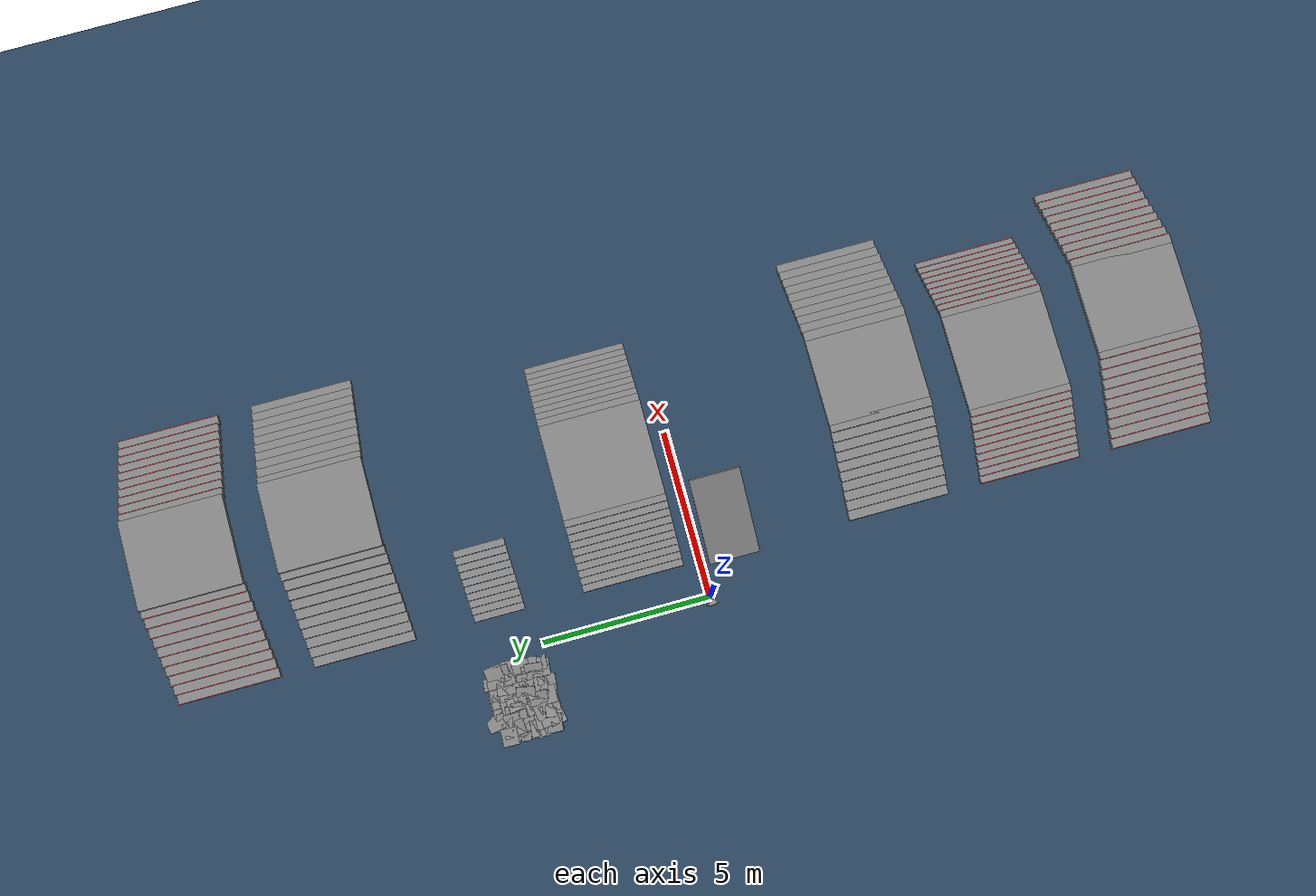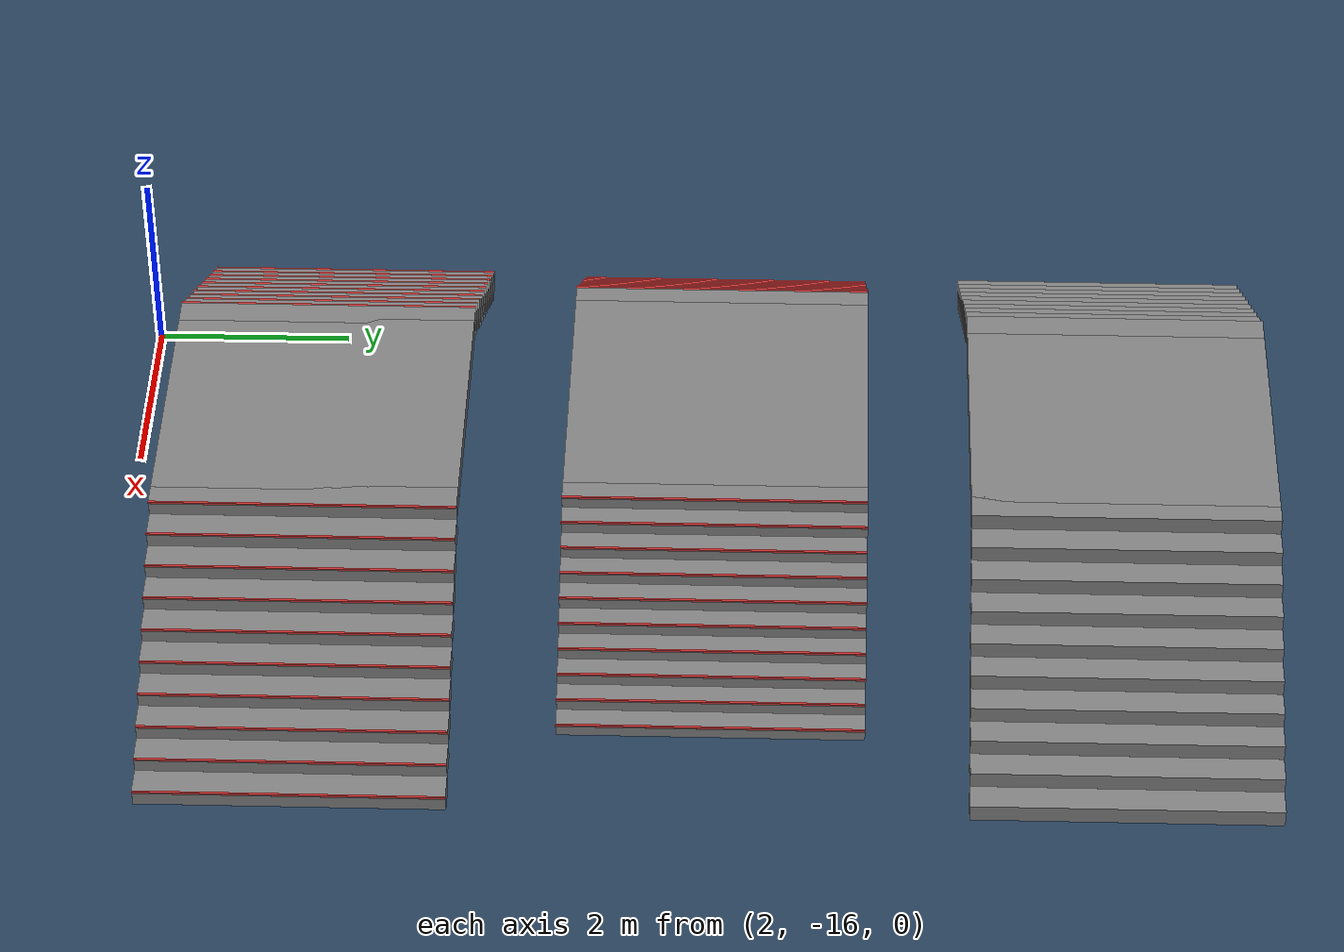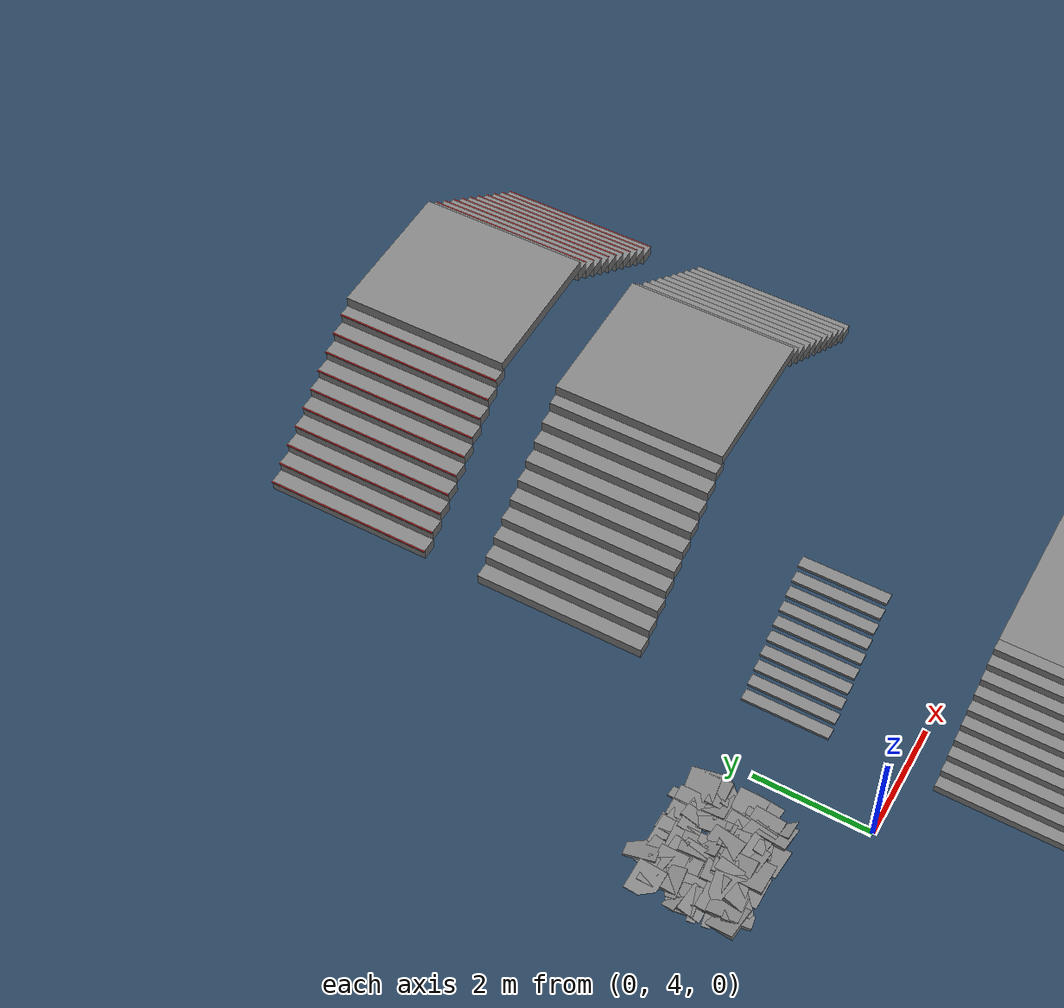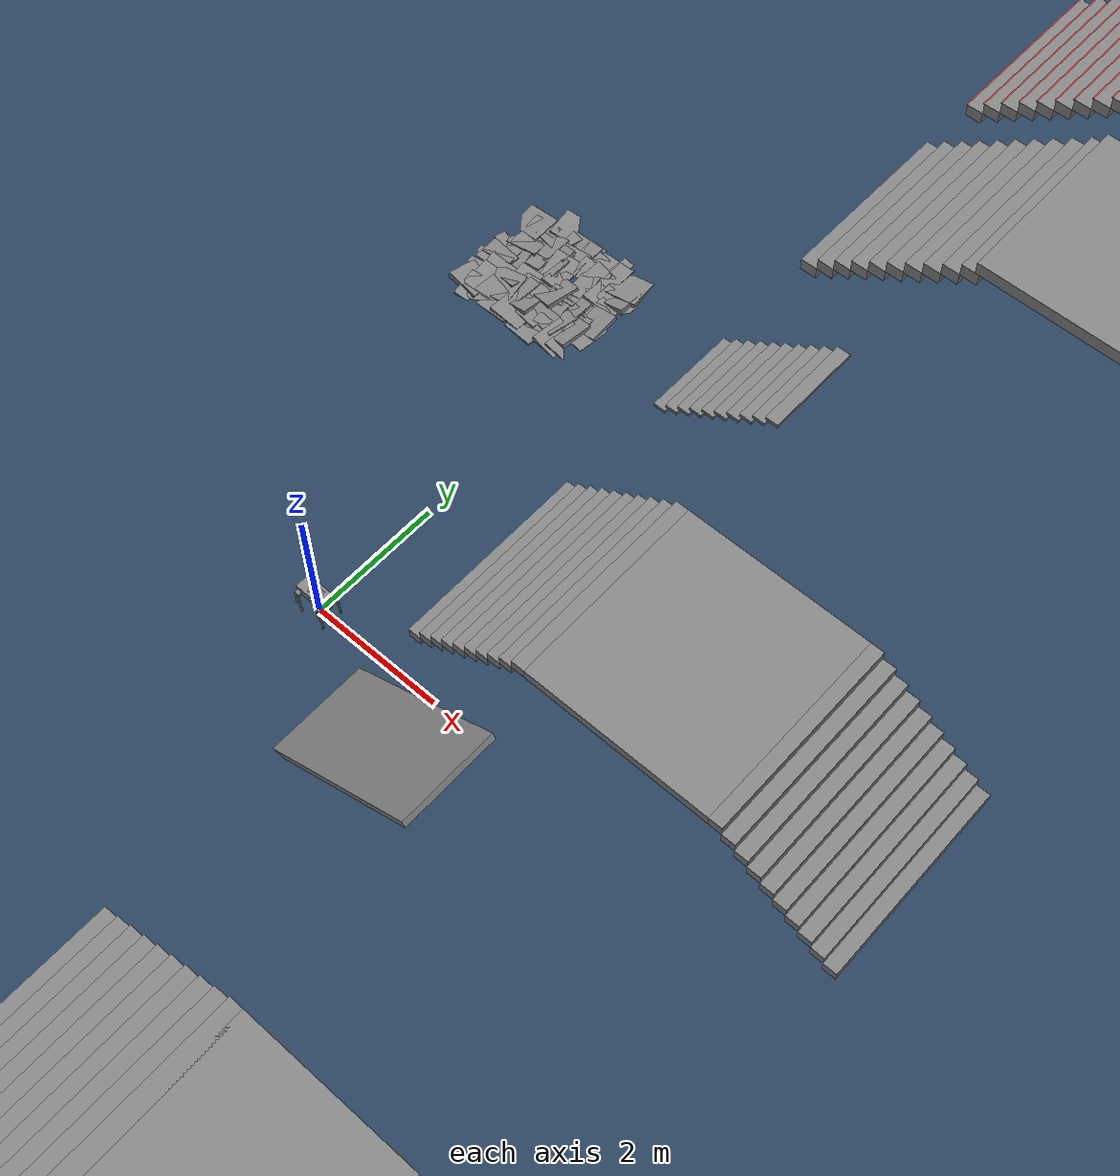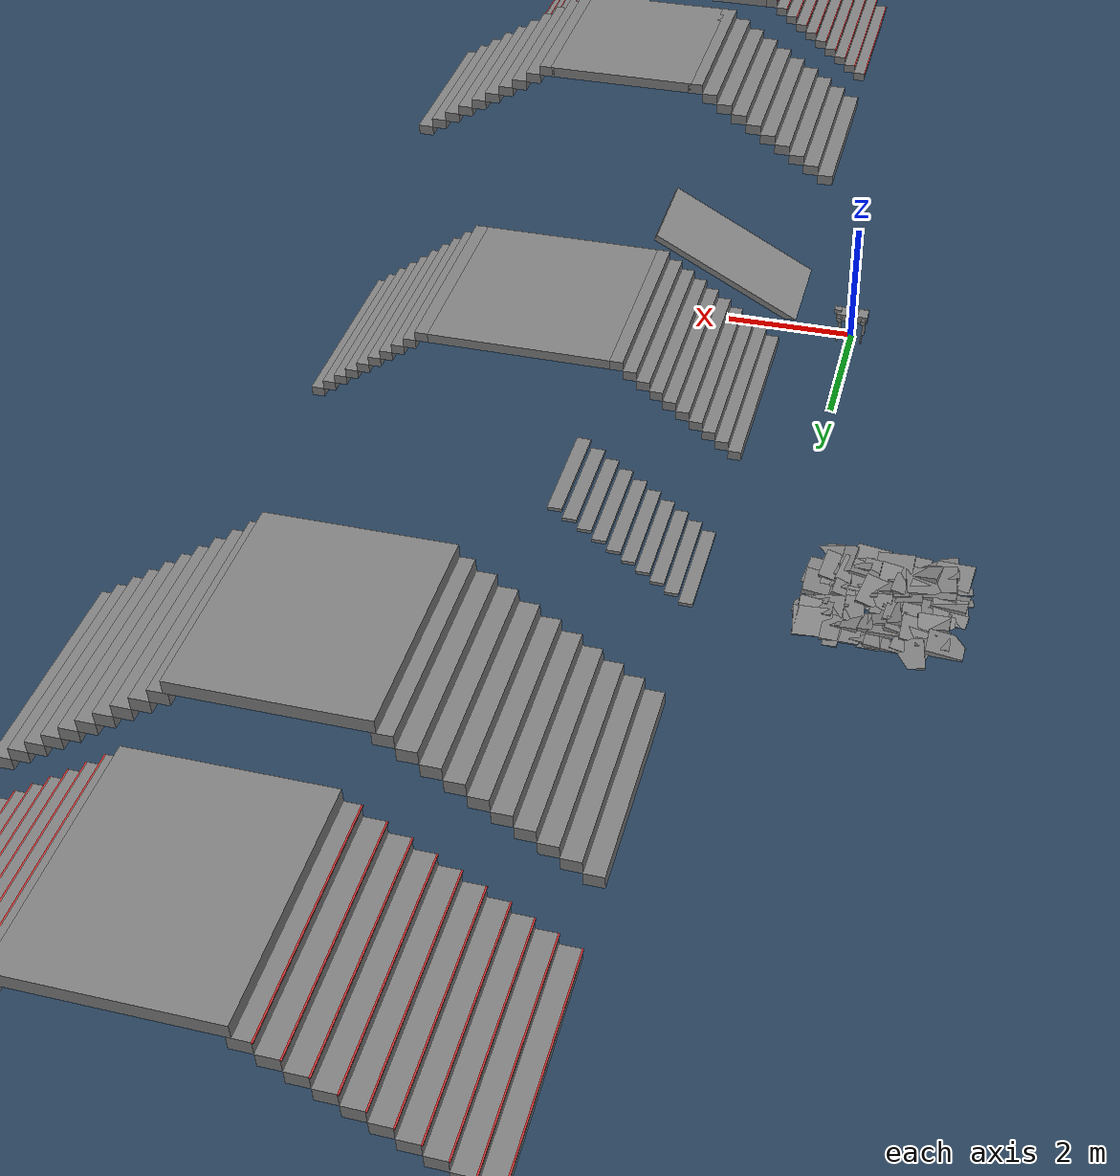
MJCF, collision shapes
<mujoco model="uni_0410 terrain scene">
  <include file="uni_0417.xml"/>

  <statistic center="0 0 0.1" extent="0.8" />

  <visual>
    <headlight diffuse="0.6 0.6 0.6" ambient="0.3 0.3 0.3" specular="0 0 0" />
    <rgba haze="0.15 0.25 0.35 1" />
    <global azimuth="-130" elevation="-20" />
  </visual>

  <asset>
    <texture type="skybox" builtin="gradient" rgb1="0.3 0.5 0.7" rgb2="0 0 0" width="512" height="3072" />
    <texture type="2d" name="groundplane" builtin="checker" mark="edge" rgb1="0.2 0.3 0.4" rgb2="0.1 0.2 0.3" markrgb="0.8 0.8 0.8" width="300" height="300" />
    <material name="groundplane" texture="groundplane" texuniform="true" texrepeat="5 5" reflectance="0.2" />

  </asset>

  <worldbody>
    <light pos="0 0 1.5" dir="0 0 -1" directional="true" />

<geom name="floor" size="0 0 0.05" type="plane" material="groundplane" />

<geom pos="2.0 -1.0 0.5" type="box" size="1.5 0.75 0.05" quat="0.968912421710645 0.0 -0.24740395925452296 0.0" />

   <!-- 台阶1 -->
<geom pos="1.2 2.0 0.075" type="box" size="0.1 1.5 0.075" quat="1.0 0.0 0.0 0.0" />
<geom pos="1.4 2.0 0.22499999999999998" type="box" size="0.1 1.5 0.075" quat="1.0 0.0 0.0 0.0" />
<geom pos="1.6 2.0 0.375" type="box" size="0.1 1.5 0.075" quat="1.0 0.0 0.0 0.0" />
<geom pos="1.8 2.0 0.525" type="box" size="0.1 1.5 0.075" quat="1.0 0.0 0.0 0.0" />
<geom pos="2.0 2.0 0.675" type="box" size="0.1 1.5 0.075" quat="1.0 0.0 0.0 0.0" />
<geom pos="2.2 2.0 0.8250000000000001" type="box" size="0.1 1.5 0.075" quat="1.0 0.0 0.0 0.0" />
<geom pos="2.4 2.0 0.9750000000000001" type="box" size="0.1 1.5 0.075" quat="1.0 0.0 0.0 0.0" />
<geom pos="2.5999999999999996 2.0 1.125" type="box" size="0.1 1.5 0.075" quat="1.0 0.0 0.0 0.0" />
<geom pos="2.8 2.0 1.275" type="box" size="0.1 1.5 0.075" quat="1.0 0.0 0.0 0.0" />
<geom pos="3.0 2.0 1.4249999999999998" type="box" size="0.1 1.5 0.075" quat="1.0 0.0 0.0 0.0" />

<geom pos="4.5 2.0 1.4249999999999998" type="box" size="1.4 1.5 0.075" quat="1.0 0.0 0.0 0.0" />
<geom pos="7.8 2.0 0.075" type="box" size="0.1 1.5 0.075" quat="1.0 0.0 0.0 0.0" />
<geom pos="7.6 2.0 0.22499999999999998" type="box" size="0.1 1.5 0.075" quat="1.0 0.0 0.0 0.0" />
<geom pos="7.4 2.0 0.375" type="box" size="0.1 1.5 0.075" quat="1.0 0.0 0.0 0.0" />
<geom pos="7.2 2.0 0.525" type="box" size="0.1 1.5 0.075" quat="1.0 0.0 0.0 0.0" />
<geom pos="7.0 2.0 0.675" type="box" size="0.1 1.5 0.075" quat="1.0 0.0 0.0 0.0" />
<geom pos="6.8 2.0 0.8250000000000001" type="box" size="0.1 1.5 0.075" quat="1.0 0.0 0.0 0.0" />
<geom pos="6.6 2.0 0.9750000000000001" type="box" size="0.1 1.5 0.075" quat="1.0 0.0 0.0 0.0" />
<geom pos="6.4 2.0 1.125" type="box" size="0.1 1.5 0.075" quat="1.0 0.0 0.0 0.0" />
<geom pos="6.2 2.0 1.275" type="box" size="0.1 1.5 0.075" quat="1.0 0.0 0.0 0.0" />
<geom pos="6.0 2.0 1.4249999999999998" type="box" size="0.1 1.5 0.075" quat="1.0 0.0 0.0 0.0" />
   <!-- 台阶1 -->

   <!-- 台阶1（带 2cm 凸起条带 / nosing），放在 y=-10 便于对比 -->
<geom pos="1.2 -10.0 0.075" type="box" size="0.1 1.5 0.075" quat="1.0 0.0 0.0 0.0" />
<geom pos="1.09 -10.0 0.14" type="box" size="0.01 1.5 0.01" quat="1.0 0.0 0.0 0.0" contype="1" conaffinity="1" condim="3" margin="0.002" rgba="0.8 0.2 0.2 1" />
<geom pos="1.4 -10.0 0.22499999999999998" type="box" size="0.1 1.5 0.075" quat="1.0 0.0 0.0 0.0" />
<geom pos="1.29 -10.0 0.29" type="box" size="0.01 1.5 0.01" quat="1.0 0.0 0.0 0.0" contype="1" conaffinity="1" condim="3" margin="0.002" rgba="0.8 0.2 0.2 1" />
<geom pos="1.6 -10.0 0.375" type="box" size="0.1 1.5 0.075" quat="1.0 0.0 0.0 0.0" />
<geom pos="1.49 -10.0 0.44" type="box" size="0.01 1.5 0.01" quat="1.0 0.0 0.0 0.0" contype="1" conaffinity="1" condim="3" margin="0.002" rgba="0.8 0.2 0.2 1" />
<geom pos="1.8 -10.0 0.525" type="box" size="0.1 1.5 0.075" quat="1.0 0.0 0.0 0.0" />
<geom pos="1.69 -10.0 0.59" type="box" size="0.01 1.5 0.01" quat="1.0 0.0 0.0 0.0" contype="1" conaffinity="1" condim="3" margin="0.002" rgba="0.8 0.2 0.2 1" />
<geom pos="2.0 -10.0 0.675" type="box" size="0.1 1.5 0.075" quat="1.0 0.0 0.0 0.0" />
<geom pos="1.89 -10.0 0.74" type="box" size="0.01 1.5 0.01" quat="1.0 0.0 0.0 0.0" contype="1" conaffinity="1" condim="3" margin="0.002" rgba="0.8 0.2 0.2 1" />
<geom pos="2.2 -10.0 0.8250000000000001" type="box" size="0.1 1.5 0.075" quat="1.0 0.0 0.0 0.0" />
<geom pos="2.09 -10.0 0.8900000000000001" type="box" size="0.01 1.5 0.01" quat="1.0 0.0 0.0 0.0" contype="1" conaffinity="1" condim="3" margin="0.002" rgba="0.8 0.2 0.2 1" />
<geom pos="2.4 -10.0 0.9750000000000001" type="box" size="0.1 1.5 0.075" quat="1.0 0.0 0.0 0.0" />
<geom pos="2.29 -10.0 1.04" type="box" size="0.01 1.5 0.01" quat="1.0 0.0 0.0 0.0" contype="1" conaffinity="1" condim="3" margin="0.002" rgba="0.8 0.2 0.2 1" />
<geom pos="2.5999999999999996 -10.0 1.125" type="box" size="0.1 1.5 0.075" quat="1.0 0.0 0.0 0.0" />
<geom pos="2.4899999999999998 -10.0 1.19" type="box" size="0.01 1.5 0.01" quat="1.0 0.0 0.0 0.0" contype="1" conaffinity="1" condim="3" margin="0.002" rgba="0.8 0.2 0.2 1" />
<geom pos="2.8 -10.0 1.275" type="box" size="0.1 1.5 0.075" quat="1.0 0.0 0.0 0.0" />
<geom pos="2.69 -10.0 1.34" type="box" size="0.01 1.5 0.01" quat="1.0 0.0 0.0 0.0" contype="1" conaffinity="1" condim="3" margin="0.002" rgba="0.8 0.2 0.2 1" />
<geom pos="3.0 -10.0 1.4249999999999998" type="box" size="0.1 1.5 0.075" quat="1.0 0.0 0.0 0.0" />
<geom pos="2.89 -10.0 1.4899999999999998" type="box" size="0.01 1.5 0.01" quat="1.0 0.0 0.0 0.0" contype="1" conaffinity="1" condim="3" margin="0.002" rgba="0.8 0.2 0.2 1" />

<geom pos="4.5 -10.0 1.4249999999999998" type="box" size="1.4 1.5 0.075" quat="1.0 0.0 0.0 0.0" />

<geom pos="7.8 -10.0 0.075" type="box" size="0.1 1.5 0.075" quat="1.0 0.0 0.0 0.0" />
<geom pos="7.91 -10.0 0.14" type="box" size="0.01 1.5 0.01" quat="1.0 0.0 0.0 0.0" contype="1" conaffinity="1" condim="3" margin="0.002" rgba="0.8 0.2 0.2 1" />
<geom pos="7.6 -10.0 0.22499999999999998" type="box" size="0.1 1.5 0.075" quat="1.0 0.0 0.0 0.0" />
<geom pos="7.71 -10.0 0.29" type="box" size="0.01 1.5 0.01" quat="1.0 0.0 0.0 0.0" contype="1" conaffinity="1" condim="3" margin="0.002" rgba="0.8 0.2 0.2 1" />
<geom pos="7.4 -10.0 0.375" type="box" size="0.1 1.5 0.075" quat="1.0 0.0 0.0 0.0" />
<geom pos="7.51 -10.0 0.44" type="box" size="0.01 1.5 0.01" quat="1.0 0.0 0.0 0.0" contype="1" conaffinity="1" condim="3" margin="0.002" rgba="0.8 0.2 0.2 1" />
<geom pos="7.2 -10.0 0.525" type="box" size="0.1 1.5 0.075" quat="1.0 0.0 0.0 0.0" />
<geom pos="7.31 -10.0 0.59" type="box" size="0.01 1.5 0.01" quat="1.0 0.0 0.0 0.0" contype="1" conaffinity="1" condim="3" margin="0.002" rgba="0.8 0.2 0.2 1" />
<geom pos="7.0 -10.0 0.675" type="box" size="0.1 1.5 0.075" quat="1.0 0.0 0.0 0.0" />
<geom pos="7.11 -10.0 0.74" type="box" size="0.01 1.5 0.01" quat="1.0 0.0 0.0 0.0" contype="1" conaffinity="1" condim="3" margin="0.002" rgba="0.8 0.2 0.2 1" />
<geom pos="6.8 -10.0 0.8250000000000001" type="box" size="0.1 1.5 0.075" quat="1.0 0.0 0.0 0.0" />
<geom pos="6.91 -10.0 0.8900000000000001" type="box" size="0.01 1.5 0.01" quat="1.0 0.0 0.0 0.0" contype="1" conaffinity="1" condim="3" margin="0.002" rgba="0.8 0.2 0.2 1" />
<geom pos="6.6 -10.0 0.9750000000000001" type="box" size="0.1 1.5 0.075" quat="1.0 0.0 0.0 0.0" />
<geom pos="6.71 -10.0 1.04" type="box" size="0.01 1.5 0.01" quat="1.0 0.0 0.0 0.0" contype="1" conaffinity="1" condim="3" margin="0.002" rgba="0.8 0.2 0.2 1" />
<geom pos="6.4 -10.0 1.125" type="box" size="0.1 1.5 0.075" quat="1.0 0.0 0.0 0.0" />
<geom pos="6.51 -10.0 1.19" type="box" size="0.01 1.5 0.01" quat="1.0 0.0 0.0 0.0" contype="1" conaffinity="1" condim="3" margin="0.002" rgba="0.8 0.2 0.2 1" />
<geom pos="6.2 -10.0 1.275" type="box" size="0.1 1.5 0.075" quat="1.0 0.0 0.0 0.0" />
<geom pos="6.31 -10.0 1.34" type="box" size="0.01 1.5 0.01" quat="1.0 0.0 0.0 0.0" contype="1" conaffinity="1" condim="3" margin="0.002" rgba="0.8 0.2 0.2 1" />
<geom pos="6.0 -10.0 1.4249999999999998" type="box" size="0.1 1.5 0.075" quat="1.0 0.0 0.0 0.0" />
<geom pos="6.11 -10.0 1.4899999999999998" type="box" size="0.01 1.5 0.01" quat="1.0 0.0 0.0 0.0" contype="1" conaffinity="1" condim="3" margin="0.002" rgba="0.8 0.2 0.2 1" />

<geom pos="1.2 6.0 0.075" type="box" size="0.1 0.75 0.024999999999999994" quat="1.0 0.0 0.0 0.0" />
<geom pos="1.4 6.0 0.22499999999999998" type="box" size="0.1 0.75 0.024999999999999994" quat="1.0 0.0 0.0 0.0" />
<geom pos="1.6 6.0 0.375" type="box" size="0.1 0.75 0.024999999999999994" quat="1.0 0.0 0.0 0.0" />
<geom pos="1.8 6.0 0.525" type="box" size="0.1 0.75 0.024999999999999994" quat="1.0 0.0 0.0 0.0" />
<geom pos="2.0 6.0 0.675" type="box" size="0.1 0.75 0.024999999999999994" quat="1.0 0.0 0.0 0.0" />
<geom pos="2.2 6.0 0.8250000000000001" type="box" size="0.1 0.75 0.024999999999999994" quat="1.0 0.0 0.0 0.0" />
<geom pos="2.4 6.0 0.9750000000000001" type="box" size="0.1 0.75 0.024999999999999994" quat="1.0 0.0 0.0 0.0" />
<geom pos="2.5999999999999996 6.0 1.125" type="box" size="0.1 0.75 0.024999999999999994" quat="1.0 0.0 0.0 0.0" />
<geom pos="2.8 6.0 1.275" type="box" size="0.1 0.75 0.024999999999999994" quat="1.0 0.0 0.0 0.0" />
<geom pos="3.0 6.0 1.4249999999999998" type="box" size="0.1 0.75 0.024999999999999994" quat="1.0 0.0 0.0 0.0" />

<!-- 20cm高 27cm宽 台阶 -->
<geom pos="1.2 10 0.1" type="box" size="0.135 1.5 0.1" quat="1.0 0.0 0.0 0.0" />
<geom pos="1.47 10 0.3" type="box" size="0.135 1.5 0.1" quat="1.0 0.0 0.0 0.0" />
<geom pos="1.74 10 0.5" type="box" size="0.135 1.5 0.1" quat="1.0 0.0 0.0 0.0" />
<geom pos="2.01 10 0.7" type="box" size="0.135 1.5 0.1" quat="1.0 0.0 0.0 0.0" />
<geom pos="2.28 10 0.9" type="box" size="0.135 1.5 0.1" quat="1.0 0.0 0.0 0.0" />
<geom pos="2.55 10 1.1" type="box" size="0.135 1.5 0.1" quat="1.0 0.0 0.0 0.0" />
<geom pos="2.82 10 1.3" type="box" size="0.135 1.5 0.1" quat="1.0 0.0 0.0 0.0" />
<geom pos="3.09 10 1.5" type="box" size="0.135 1.5 0.1" quat="1.0 0.0 0.0 0.0" />
<geom pos="3.36 10 1.7" type="box" size="0.135 1.5 0.1" quat="1.0 0.0 0.0 0.0" />
<geom pos="3.63 10 1.9" type="box" size="0.135 1.5 0.1" quat="1.0 0.0 0.0 0.0" />
<geom pos="5 10 2.1" type="box" size="1.3 1.5 0.1" quat="1.0 0.0 0.0 0.0" />

<geom pos="8.8 10 0.1" type="box" size="0.135 1.5 0.1" quat="1.0 0.0 0.0 0.0" />
<geom pos="8.53 10 0.3" type="box" size="0.135 1.5 0.1" quat="1.0 0.0 0.0 0.0" />
<geom pos="8.26 10 0.5" type="box" size="0.135 1.5 0.1" quat="1.0 0.0 0.0 0.0" />
<geom pos="7.99 10 0.7" type="box" size="0.135 1.5 0.1" quat="1.0 0.0 0.0 0.0" />
<geom pos="7.72 10 0.9" type="box" size="0.135 1.5 0.1" quat="1.0 0.0 0.0 0.0" />
<geom pos="7.45 10 1.1" type="box" size="0.135 1.5 0.1" quat="1.0 0.0 0.0 0.0" />
<geom pos="7.18 10 1.3" type="box" size="0.135 1.5 0.1" quat="1.0 0.0 0.0 0.0" />
<geom pos="6.91 10 1.5" type="box" size="0.135 1.5 0.1" quat="1.0 0.0 0.0 0.0" />
<geom pos="6.64 10 1.7" type="box" size="0.135 1.5 0.1" quat="1.0 0.0 0.0 0.0" />
<geom pos="6.37 10 1.9" type="box" size="0.135 1.5 0.1" quat="1.0 0.0 0.0 0.0" />

<!-- 20cm高 27cm宽 台阶（带 2cm 凸起条带 / nosing），放在 y=14 便于对比 -->
<geom pos="1.2 14 0.1" type="box" size="0.135 1.5 0.1" quat="1.0 0.0 0.0 0.0" />
<geom pos="1.055 14 0.19" type="box" size="0.01 1.5 0.01" quat="1.0 0.0 0.0 0.0" contype="1" conaffinity="1" condim="3" margin="0.002" rgba="0.8 0.2 0.2 1" />
<geom pos="1.47 14 0.3" type="box" size="0.135 1.5 0.1" quat="1.0 0.0 0.0 0.0" />
<geom pos="1.325 14 0.39" type="box" size="0.01 1.5 0.01" quat="1.0 0.0 0.0 0.0" contype="1" conaffinity="1" condim="3" margin="0.002" rgba="0.8 0.2 0.2 1" />
<geom pos="1.74 14 0.5" type="box" size="0.135 1.5 0.1" quat="1.0 0.0 0.0 0.0" />
<geom pos="1.595 14 0.59" type="box" size="0.01 1.5 0.01" quat="1.0 0.0 0.0 0.0" contype="1" conaffinity="1" condim="3" margin="0.002" rgba="0.8 0.2 0.2 1" />
<geom pos="2.01 14 0.7" type="box" size="0.135 1.5 0.1" quat="1.0 0.0 0.0 0.0" />
<geom pos="1.865 14 0.7899999999999999" type="box" size="0.01 1.5 0.01" quat="1.0 0.0 0.0 0.0" contype="1" conaffinity="1" condim="3" margin="0.002" rgba="0.8 0.2 0.2 1" />
<geom pos="2.28 14 0.9" type="box" size="0.135 1.5 0.1" quat="1.0 0.0 0.0 0.0" />
<geom pos="2.135 14 0.99" type="box" size="0.01 1.5 0.01" quat="1.0 0.0 0.0 0.0" contype="1" conaffinity="1" condim="3" margin="0.002" rgba="0.8 0.2 0.2 1" />
<geom pos="2.55 14 1.1" type="box" size="0.135 1.5 0.1" quat="1.0 0.0 0.0 0.0" />
<geom pos="2.405 14 1.1900000000000002" type="box" size="0.01 1.5 0.01" quat="1.0 0.0 0.0 0.0" contype="1" conaffinity="1" condim="3" margin="0.002" rgba="0.8 0.2 0.2 1" />
<geom pos="2.82 14 1.3" type="box" size="0.135 1.5 0.1" quat="1.0 0.0 0.0 0.0" />
<geom pos="2.675 14 1.39" type="box" size="0.01 1.5 0.01" quat="1.0 0.0 0.0 0.0" contype="1" conaffinity="1" condim="3" margin="0.002" rgba="0.8 0.2 0.2 1" />
<geom pos="3.09 14 1.5" type="box" size="0.135 1.5 0.1" quat="1.0 0.0 0.0 0.0" />
<geom pos="2.945 14 1.5899999999999999" type="box" size="0.01 1.5 0.01" quat="1.0 0.0 0.0 0.0" contype="1" conaffinity="1" condim="3" margin="0.002" rgba="0.8 0.2 0.2 1" />
<geom pos="3.36 14 1.7" type="box" size="0.135 1.5 0.1" quat="1.0 0.0 0.0 0.0" />
<geom pos="3.215 14 1.79" type="box" size="0.01 1.5 0.01" quat="1.0 0.0 0.0 0.0" contype="1" conaffinity="1" condim="3" margin="0.002" rgba="0.8 0.2 0.2 1" />
<geom pos="3.63 14 1.9" type="box" size="0.135 1.5 0.1" quat="1.0 0.0 0.0 0.0" />
<geom pos="3.485 14 1.99" type="box" size="0.01 1.5 0.01" quat="1.0 0.0 0.0 0.0" contype="1" conaffinity="1" condim="3" margin="0.002" rgba="0.8 0.2 0.2 1" />
<geom pos="5 14 2.1" type="box" size="1.3 1.5 0.1" quat="1.0 0.0 0.0 0.0" />

<geom pos="8.8 14 0.1" type="box" size="0.135 1.5 0.1" quat="1.0 0.0 0.0 0.0" />
<geom pos="8.945 14 0.19" type="box" size="0.01 1.5 0.01" quat="1.0 0.0 0.0 0.0" contype="1" conaffinity="1" condim="3" margin="0.002" rgba="0.8 0.2 0.2 1" />
<geom pos="8.53 14 0.3" type="box" size="0.135 1.5 0.1" quat="1.0 0.0 0.0 0.0" />
<geom pos="8.675 14 0.39" type="box" size="0.01 1.5 0.01" quat="1.0 0.0 0.0 0.0" contype="1" conaffinity="1" condim="3" margin="0.002" rgba="0.8 0.2 0.2 1" />
<geom pos="8.26 14 0.5" type="box" size="0.135 1.5 0.1" quat="1.0 0.0 0.0 0.0" />
<geom pos="8.405 14 0.59" type="box" size="0.01 1.5 0.01" quat="1.0 0.0 0.0 0.0" contype="1" conaffinity="1" condim="3" margin="0.002" rgba="0.8 0.2 0.2 1" />
<geom pos="7.99 14 0.7" type="box" size="0.135 1.5 0.1" quat="1.0 0.0 0.0 0.0" />
<geom pos="8.135 14 0.7899999999999999" type="box" size="0.01 1.5 0.01" quat="1.0 0.0 0.0 0.0" contype="1" conaffinity="1" condim="3" margin="0.002" rgba="0.8 0.2 0.2 1" />
<geom pos="7.72 14 0.9" type="box" size="0.135 1.5 0.1" quat="1.0 0.0 0.0 0.0" />
<geom pos="7.865 14 0.99" type="box" size="0.01 1.5 0.01" quat="1.0 0.0 0.0 0.0" contype="1" conaffinity="1" condim="3" margin="0.002" rgba="0.8 0.2 0.2 1" />
<geom pos="7.45 14 1.1" type="box" size="0.135 1.5 0.1" quat="1.0 0.0 0.0 0.0" />
<geom pos="7.595 14 1.1900000000000002" type="box" size="0.01 1.5 0.01" quat="1.0 0.0 0.0 0.0" contype="1" conaffinity="1" condim="3" margin="0.002" rgba="0.8 0.2 0.2 1" />
<geom pos="7.18 14 1.3" type="box" size="0.135 1.5 0.1" quat="1.0 0.0 0.0 0.0" />
<geom pos="7.325 14 1.39" type="box" size="0.01 1.5 0.01" quat="1.0 0.0 0.0 0.0" contype="1" conaffinity="1" condim="3" margin="0.002" rgba="0.8 0.2 0.2 1" />
<geom pos="6.91 14 1.5" type="box" size="0.135 1.5 0.1" quat="1.0 0.0 0.0 0.0" />
<geom pos="7.055 14 1.5899999999999999" type="box" size="0.01 1.5 0.01" quat="1.0 0.0 0.0 0.0" contype="1" conaffinity="1" condim="3" margin="0.002" rgba="0.8 0.2 0.2 1" />
<geom pos="6.64 14 1.7" type="box" size="0.135 1.5 0.1" quat="1.0 0.0 0.0 0.0" />
<geom pos="6.785 14 1.79" type="box" size="0.01 1.5 0.01" quat="1.0 0.0 0.0 0.0" contype="1" conaffinity="1" condim="3" margin="0.002" rgba="0.8 0.2 0.2 1" />
<geom pos="6.37 14 1.9" type="box" size="0.135 1.5 0.1" quat="1.0 0.0 0.0 0.0" />
<geom pos="6.515 14 1.99" type="box" size="0.01 1.5 0.01" quat="1.0 0.0 0.0 0.0" contype="1" conaffinity="1" condim="3" margin="0.002" rgba="0.8 0.2 0.2 1" />

<!-- 17cm高 27cm宽 台阶 -->
<geom pos="1.2 -6 0.085" type="box" size="0.135 1.5 0.09" quat="1.0 0.0 0.0 0.0" />
<geom pos="1.47 -6 0.255" type="box" size="0.135 1.5 0.09" quat="1.0 0.0 0.0 0.0" />
<geom pos="1.74 -6 0.425" type="box" size="0.135 1.5 0.09" quat="1.0 0.0 0.0 0.0" />
<geom pos="2.01 -6 0.595" type="box" size="0.135 1.5 0.09" quat="1.0 0.0 0.0 0.0" />
<geom pos="2.28 -6 0.765" type="box" size="0.135 1.5 0.09" quat="1.0 0.0 0.0 0.0" />
<geom pos="2.55 -6 0.935" type="box" size="0.135 1.5 0.09" quat="1.0 0.0 0.0 0.0" />
<geom pos="2.82 -6 1.105" type="box" size="0.135 1.5 0.09" quat="1.0 0.0 0.0 0.0" />
<geom pos="3.09 -6 1.275" type="box" size="0.135 1.5 0.09" quat="1.0 0.0 0.0 0.0" />
<geom pos="3.36 -6 1.445" type="box" size="0.135 1.5 0.09" quat="1.0 0.0 0.0 0.0" />
<geom pos="3.63 -6 1.615" type="box" size="0.135 1.5 0.09" quat="1.0 0.0 0.0 0.0" />
<geom pos="5 -6 1.615" type="box" size="1.3 1.5 0.09" quat="1.0 0.0 0.0 0.0" />

<geom pos="8.8 -6 0.085" type="box" size="0.135 1.5 0.09" quat="1.0 0.0 0.0 0.0" />
<geom pos="8.53 -6 0.255" type="box" size="0.135 1.5 0.09" quat="1.0 0.0 0.0 0.0" />
<geom pos="8.26 -6 0.425" type="box" size="0.135 1.5 0.09" quat="1.0 0.0 0.0 0.0" />
<geom pos="7.99 -6 0.595" type="box" size="0.135 1.5 0.09" quat="1.0 0.0 0.0 0.0" />
<geom pos="7.72 -6 0.765" type="box" size="0.135 1.5 0.09" quat="1.0 0.0 0.0 0.0" />
<geom pos="7.45 -6 0.935" type="box" size="0.135 1.5 0.09" quat="1.0 0.0 0.0 0.0" />
<geom pos="7.18 -6 1.105" type="box" size="0.135 1.5 0.09" quat="1.0 0.0 0.0 0.0" />
<geom pos="6.91 -6 1.275" type="box" size="0.135 1.5 0.09" quat="1.0 0.0 0.0 0.0" />
<geom pos="6.64 -6 1.445" type="box" size="0.135 1.5 0.09" quat="1.0 0.0 0.0 0.0" />
<geom pos="6.37 -6 1.615" type="box" size="0.135 1.5 0.09" quat="1.0 0.0 0.0 0.0" />

<!-- 17cm高 27cm宽 台阶（带 2cm 凸起条带 / nosing），放在 y=-14 便于对比 -->
<geom pos="1.2 -14 0.085" type="box" size="0.135 1.5 0.09" quat="1.0 0.0 0.0 0.0" />
<geom pos="1.055 -14 0.165" type="box" size="0.01 1.5 0.01" quat="1.0 0.0 0.0 0.0" contype="1" conaffinity="1" condim="3" margin="0.002" rgba="0.8 0.2 0.2 1" />
<geom pos="1.47 -14 0.255" type="box" size="0.135 1.5 0.09" quat="1.0 0.0 0.0 0.0" />
<geom pos="1.325 -14 0.335" type="box" size="0.01 1.5 0.01" quat="1.0 0.0 0.0 0.0" contype="1" conaffinity="1" condim="3" margin="0.002" rgba="0.8 0.2 0.2 1" />
<geom pos="1.74 -14 0.425" type="box" size="0.135 1.5 0.09" quat="1.0 0.0 0.0 0.0" />
<geom pos="1.595 -14 0.505" type="box" size="0.01 1.5 0.01" quat="1.0 0.0 0.0 0.0" contype="1" conaffinity="1" condim="3" margin="0.002" rgba="0.8 0.2 0.2 1" />
<geom pos="2.01 -14 0.595" type="box" size="0.135 1.5 0.09" quat="1.0 0.0 0.0 0.0" />
<geom pos="1.865 -14 0.675" type="box" size="0.01 1.5 0.01" quat="1.0 0.0 0.0 0.0" contype="1" conaffinity="1" condim="3" margin="0.002" rgba="0.8 0.2 0.2 1" />
<geom pos="2.28 -14 0.765" type="box" size="0.135 1.5 0.09" quat="1.0 0.0 0.0 0.0" />
<geom pos="2.135 -14 0.845" type="box" size="0.01 1.5 0.01" quat="1.0 0.0 0.0 0.0" contype="1" conaffinity="1" condim="3" margin="0.002" rgba="0.8 0.2 0.2 1" />
<geom pos="2.55 -14 0.935" type="box" size="0.135 1.5 0.09" quat="1.0 0.0 0.0 0.0" />
<geom pos="2.405 -14 1.015" type="box" size="0.01 1.5 0.01" quat="1.0 0.0 0.0 0.0" contype="1" conaffinity="1" condim="3" margin="0.002" rgba="0.8 0.2 0.2 1" />
<geom pos="2.82 -14 1.105" type="box" size="0.135 1.5 0.09" quat="1.0 0.0 0.0 0.0" />
<geom pos="2.675 -14 1.185" type="box" size="0.01 1.5 0.01" quat="1.0 0.0 0.0 0.0" contype="1" conaffinity="1" condim="3" margin="0.002" rgba="0.8 0.2 0.2 1" />
<geom pos="3.09 -14 1.275" type="box" size="0.135 1.5 0.09" quat="1.0 0.0 0.0 0.0" />
<geom pos="2.945 -14 1.355" type="box" size="0.01 1.5 0.01" quat="1.0 0.0 0.0 0.0" contype="1" conaffinity="1" condim="3" margin="0.002" rgba="0.8 0.2 0.2 1" />
<geom pos="3.36 -14 1.445" type="box" size="0.135 1.5 0.09" quat="1.0 0.0 0.0 0.0" />
<geom pos="3.215 -14 1.525" type="box" size="0.01 1.5 0.01" quat="1.0 0.0 0.0 0.0" contype="1" conaffinity="1" condim="3" margin="0.002" rgba="0.8 0.2 0.2 1" />
<geom pos="3.63 -14 1.615" type="box" size="0.135 1.5 0.09" quat="1.0 0.0 0.0 0.0" />
<geom pos="3.485 -14 1.695" type="box" size="0.01 1.5 0.01" quat="1.0 0.0 0.0 0.0" contype="1" conaffinity="1" condim="3" margin="0.002" rgba="0.8 0.2 0.2 1" />
<geom pos="5 -14 1.615" type="box" size="1.3 1.5 0.09" quat="1.0 0.0 0.0 0.0" />

<geom pos="8.8 -14 0.085" type="box" size="0.135 1.5 0.09" quat="1.0 0.0 0.0 0.0" />
<geom pos="8.945 -14 0.165" type="box" size="0.01 1.5 0.01" quat="1.0 0.0 0.0 0.0" contype="1" conaffinity="1" condim="3" margin="0.002" rgba="0.8 0.2 0.2 1" />
<geom pos="8.53 -14 0.255" type="box" size="0.135 1.5 0.09" quat="1.0 0.0 0.0 0.0" />
<geom pos="8.675 -14 0.335" type="box" size="0.01 1.5 0.01" quat="1.0 0.0 0.0 0.0" contype="1" conaffinity="1" condim="3" margin="0.002" rgba="0.8 0.2 0.2 1" />
<geom pos="8.26 -14 0.425" type="box" size="0.135 1.5 0.09" quat="1.0 0.0 0.0 0.0" />
<geom pos="8.405 -14 0.505" type="box" size="0.01 1.5 0.01" quat="1.0 0.0 0.0 0.0" contype="1" conaffinity="1" condim="3" margin="0.002" rgba="0.8 0.2 0.2 1" />
<geom pos="7.99 -14 0.595" type="box" size="0.135 1.5 0.09" quat="1.0 0.0 0.0 0.0" />
<geom pos="8.135 -14 0.675" type="box" size="0.01 1.5 0.01" quat="1.0 0.0 0.0 0.0" contype="1" conaffinity="1" condim="3" margin="0.002" rgba="0.8 0.2 0.2 1" />
<geom pos="7.72 -14 0.765" type="box" size="0.135 1.5 0.09" quat="1.0 0.0 0.0 0.0" />
<geom pos="7.865 -14 0.845" type="box" size="0.01 1.5 0.01" quat="1.0 0.0 0.0 0.0" contype="1" conaffinity="1" condim="3" margin="0.002" rgba="0.8 0.2 0.2 1" />
<geom pos="7.45 -14 0.935" type="box" size="0.135 1.5 0.09" quat="1.0 0.0 0.0 0.0" />
<geom pos="7.595 -14 1.015" type="box" size="0.01 1.5 0.01" quat="1.0 0.0 0.0 0.0" contype="1" conaffinity="1" condim="3" margin="0.002" rgba="0.8 0.2 0.2 1" />
<geom pos="7.18 -14 1.105" type="box" size="0.135 1.5 0.09" quat="1.0 0.0 0.0 0.0" />
<geom pos="7.325 -14 1.185" type="box" size="0.01 1.5 0.01" quat="1.0 0.0 0.0 0.0" contype="1" conaffinity="1" condim="3" margin="0.002" rgba="0.8 0.2 0.2 1" />
<geom pos="6.91 -14 1.275" type="box" size="0.135 1.5 0.09" quat="1.0 0.0 0.0 0.0" />
<geom pos="7.055 -14 1.355" type="box" size="0.01 1.5 0.01" quat="1.0 0.0 0.0 0.0" contype="1" conaffinity="1" condim="3" margin="0.002" rgba="0.8 0.2 0.2 1" />
<geom pos="6.64 -14 1.445" type="box" size="0.135 1.5 0.09" quat="1.0 0.0 0.0 0.0" />
<geom pos="6.785 -14 1.525" type="box" size="0.01 1.5 0.01" quat="1.0 0.0 0.0 0.0" contype="1" conaffinity="1" condim="3" margin="0.002" rgba="0.8 0.2 0.2 1" />
<geom pos="6.37 -14 1.615" type="box" size="0.135 1.5 0.09" quat="1.0 0.0 0.0 0.0" />
<geom pos="6.515 -14 1.695" type="box" size="0.01 1.5 0.01" quat="1.0 0.0 0.0 0.0" contype="1" conaffinity="1" condim="3" margin="0.002" rgba="0.8 0.2 0.2 1" />

<geom pos="-2.3004568480001155 5.230133099821309 -0.25" type="box" size="0.2667418434232123 0.23249216246593754 0.2715603840154582" quat="0.9937514109759715 -0.09011523303710722 0.04584049177774514 -0.04728665003473938" />
<geom pos="-2.3004568480001155 5.391515746812814 -0.25" type="box" size="0.2505265313539923 0.2412016313894627 0.2264599735410741" quat="0.9947855832976967 0.0430479213794962 0.004496328850963352 0.0923488102512985" />
<geom pos="-2.3004568480001155 5.632708194664771 -0.25" type="box" size="0.2744568938089314 0.24992449427731162 0.22801643019685697" quat="0.9927267717486197 0.07160131296835394 -0.005361370104009311 0.09663366051940456" />
<geom pos="-2.3004568480001155 5.798990692476225 -0.25" type="box" size="0.24325500647900072 0.2253568952181176 0.26629093934549475" quat="0.9942381647366705 0.09525301325965287 0.00794678229822832 -0.048519932987572345" />
<geom pos="-2.3004568480001155 5.973541127254212 -0.25" type="box" size="0.2398510354361266 0.24285052907373605 0.26474659664781297" quat="0.9964084612238755 -0.04106533003165011 -0.0363795415854814 0.06450074437470632" />
<geom pos="-2.3004568480001155 6.1770510315939235 -0.25" type="box" size="0.25720829764278585 0.23711879563200236 0.22878298749776027" quat="0.9937658772683013 -0.08834725270306294 0.0169573991826565 -0.06585279591592566" />
<geom pos="-2.3004568480001155 6.407180520840007 -0.25" type="box" size="0.24754562515074474 0.25947160159627974 0.23928331743280107" quat="0.9958964892628885 0.04305664599570697 -0.045399565427206114 0.0653849169799509" />
<geom pos="-2.3004568480001155 6.629340270719652 -0.25" type="box" size="0.2547590853159438 0.2314305783929404 0.268237133040538" quat="0.9972993669391019 0.044601800582484905 -0.05693885512370222 -0.012752210195468728" />
<geom pos="-2.1403960142105545 5.169451405171494 -0.25" type="box" size="0.24860553780818326 0.2298644058617868 0.2557271181931712" quat="0.9914709750904385 0.03140703504746152 0.09964006753412274 0.07791508611647713" />
<geom pos="-2.1403960142105545 5.365443034016214 -0.25" type="box" size="0.2291512386430681 0.25867181712863563 0.27347983292603073" quat="0.9971489888939771 -0.012801738465963004 0.06299248639499276 0.039521590273487665" />
<geom pos="-2.1403960142105545 5.564856717019695 -0.25" type="box" size="0.23402731407731425 0.26579436660697997 0.2553901560684408" quat="0.9966301905043169 0.07818366455605208 0.024123866909938566 0.005798018388017237" />
<geom pos="-2.1403960142105545 5.718290300524951 -0.25" type="box" size="0.26305873229776777 0.22976833293040352 0.2368622332864588" quat="0.9965179080213955 0.04103949917917902 0.06351715359390735 0.035119648334118" />
<geom pos="-2.1403960142105545 5.937021976021513 -0.25" type="box" size="0.25829997576988234 0.23777318710233433 0.24146425783496483" quat="0.9934945982010286 0.06600502560370954 -0.06390951813814603 0.06728590812183728" />
<geom pos="-2.1403960142105545 6.139922384241892 -0.25" type="box" size="0.23653538925627735 0.2436978135416446 0.240333142471557" quat="0.9965532548871666 0.03912419743215279 0.07314101139716957 0.0011400881032193077" />
<geom pos="-2.1403960142105545 6.301771003196722 -0.25" type="box" size="0.2531389078197739 0.24480016352294456 0.2504805521908677" quat="0.9929737504129765 -0.09338521837305551 -0.05209114295204799 0.05068377261169358" />
<geom pos="-2.1403960142105545 6.507865639382873 -0.25" type="box" size="0.2276301834358782 0.26649607136000125 0.257729055845175" quat="0.9978879006215207 0.06064426844548832 -0.013463574733080436 0.01899322651086425" />
<geom pos="-1.8913580852312173 5.241268832370592 -0.25" type="box" size="0.2626219760929962 0.24411637158707777 0.2607077194593069" quat="0.9875355197654081 0.10169530993875045 0.08550302030532102 -0.0843853936223203" />
<geom pos="-1.8913580852312173 5.471949466771439 -0.25" type="box" size="0.2602767497051143 0.273953920565642 0.27337839148294096" quat="0.9958713146560139 0.025763189149319767 -0.029456230012379816 0.08190795592381117" />
<geom pos="-1.8913580852312173 5.710208626029221 -0.25" type="box" size="0.23410940494091387 0.2367080582839282 0.24568630976566702" quat="0.9897189155738972 -0.08734156791079449 -0.08044028159717216 -0.07973255148733269" />
<geom pos="-1.8913580852312173 5.955348349118732 -0.25" type="box" size="0.23982897662316305 0.23800117277662278 0.2398222460937144" quat="0.9952418019176436 0.05430372873578345 -0.07866554086694699 0.018883681876785678" />
<geom pos="-1.8913580852312173 6.185979720159965 -0.25" type="box" size="0.2462147197863695 0.23219524695551647 0.2711440904263542" quat="0.9982254065785714 -0.011567722302419247 -0.05642983491193701 0.015096330467764624" />
<geom pos="-1.8913580852312173 6.4251426885516025 -0.25" type="box" size="0.23523910319808664 0.23480755129856565 0.2692163752500142" quat="0.9968448648091833 -0.003964163248548163 -0.07915930034105623 0.004290231091029004" />
<geom pos="-1.8913580852312173 6.632084792336812 -0.25" type="box" size="0.2603836051705248 0.2293842626424212 0.26630834239542744" quat="0.9942544585183625 -0.03847116757612908 -0.015013446725097508 -0.09875544237721844" />
<geom pos="-1.8913580852312173 6.8677842882805304 -0.25" type="box" size="0.22682173018977822 0.25620373771208627 0.2590106178200968" quat="0.9917966349039323 -0.04622336464814654 0.08055478391174208 0.08782802709142892" />
<geom pos="-1.6798294713431876 5.216238277949043 -0.25" type="box" size="0.2632521212844899 0.2402658144953708 0.24841784794218005" quat="0.9997799409897189 -0.003276721590235065 -0.020688201582637684 -0.0011536921125319332" />
<geom pos="-1.6798294713431876 5.386856114907906 -0.25" type="box" size="0.26672713061026987 0.24844660721532208 0.23313692749728976" quat="0.9952829473710711 0.07407221696833978 -0.013859958088202382 -0.061098796285541615" />
<geom pos="-1.6798294713431876 5.591071097018706 -0.25" type="box" size="0.23246847630546943 0.25230360402816476 0.26125984794942364" quat="0.9935207484320158 0.05042174247872936 -0.08002771662650093 -0.06300583220658486" />
<geom pos="-1.6798294713431876 5.741842048926222 -0.25" type="box" size="0.2535630104904315 0.24795359449084495 0.2463449562851746" quat="0.9940727390106978 0.07645301721135746 0.05888786747389042 0.0500654050161026" />
<geom pos="-1.6798294713431876 5.905363306176914 -0.25" type="box" size="0.27072344768948214 0.22692489903878324 0.25032679935595825" quat="0.9977180574934882 0.021245636186625227 -0.03211110830763 -0.05546329793388168" />
<geom pos="-1.6798294713431876 6.15296609717695 -0.25" type="box" size="0.27075061156330754 0.2600061673600183 0.2621071701382346" quat="0.9954121140543586 0.05159092291611383 -0.07045052751410034 -0.039112952323769316" />
<geom pos="-1.6798294713431876 6.366743216660697 -0.25" type="box" size="0.23450857272964362 0.2407163023193743 0.2666025413500864" quat="0.9922247127582067 0.07575177513114786 -0.09279467536142899 -0.03377774683043695" />
<geom pos="-1.6798294713431876 6.551643355280989 -0.25" type="box" size="0.26049187301894283 0.27022426120507964 0.23971723837257095" quat="0.9892928509960738 -0.10100280472577938 -0.0600366609488913 -0.0865660889014509" />
<geom pos="-1.4765163584841376 5.243937334992851 -0.25" type="box" size="0.26136834696977396 0.2523172670818107 0.2654694500155096" quat="0.9985049365903822 -0.02950096022889073 0.04556436314956665 -0.00644001249885379" />
<geom pos="-1.4765163584841376 5.480410750662077 -0.25" type="box" size="0.2440914363505842 0.25654690520997264 0.2583881995141055" quat="0.9933328589616501 -0.06913812509184492 -0.09136238609169695 -0.012754033616475648" />
<geom pos="-1.4765163584841376 5.671235516827659 -0.25" type="box" size="0.267137477516981 0.23005560417856358 0.24452561156808555" quat="0.9940257850736071 0.051254350696765066 0.06721387336133489 0.06905088972068747" />
<geom pos="-1.4765163584841376 5.845102562083532 -0.25" type="box" size="0.25941410073895627 0.24466997366532126 0.24443215657180062" quat="0.9984794775297112 0.04477338473757268 0.03200898692652765 0.0030824871571849344" />
<geom pos="-1.4765163584841376 6.010575440437007 -0.25" type="box" size="0.26435857520274697 0.23236342580867092 0.24142028047228445" quat="0.9988398514879413 0.024463332973345336 -0.03172619531082579 0.026719748323726804" />
<geom pos="-1.4765163584841376 6.23782046041485 -0.25" type="box" size="0.24731691273440778 0.25843666448052316 0.2710876107672864" quat="0.9885864324283745 0.08290722719127752 0.09790149547395594 0.07898452052114466" />
<geom pos="-1.4765163584841376 6.44930631573619 -0.25" type="box" size="0.24193344533885286 0.23138582308048286 0.26168496711942596" quat="0.9958233764692439 0.07917403843656666 -0.02581247498391686 0.03742980964745321" />
<geom pos="-1.4765163584841376 6.684566195548674 -0.25" type="box" size="0.2472173291178155 0.22976521336220676 0.24579788179058876" quat="0.9972709256786985 0.05344665943858395 -0.04768801960369878 -0.01788877237504326" />
<geom pos="-1.2836828006996281 5.233446740475545 -0.25" type="box" size="0.270942684859463 0.26600855236486054 0.2296077997678793" quat="0.9990002946606846 0.04415559586693775 -0.005684427367154231 -0.004047456856993205" />
<geom pos="-1.2836828006996281 5.446684944046352 -0.25" type="box" size="0.27057165150527335 0.26104170501325036 0.24775613085616044" quat="0.9973272818901999 -0.03585324604105891 -0.0027768638379429824 -0.0636013095230833" />
<geom pos="-1.2836828006996281 5.611103486144901 -0.25" type="box" size="0.2581954354219156 0.2469368219651923 0.24036756098125636" quat="0.9936312966887875 0.09017870480124786 0.06642617029778168 -0.012337396017719982" />
<geom pos="-1.2836828006996281 5.849517593571514 -0.25" type="box" size="0.27467145474022 0.27400068490578466 0.2735778012229137" quat="0.9916347981074018 -0.026604654441189333 -0.09638112447022586 -0.08162902909144508" />
<geom pos="-1.2836828006996281 6.08784409988581 -0.25" type="box" size="0.2572816459813805 0.259301331764223 0.2497915058099132" quat="0.9950820743411886 -0.09067596276893386 0.03956525467724424 0.004911794284056946" />
<geom pos="-1.2836828006996281 6.268302962193964 -0.25" type="box" size="0.26840679557573427 0.24608249031753818 0.23034148085004616" quat="0.9987264631057741 -0.005999555326392561 0.04977616980667998 0.005638275223276664" />
<geom pos="-1.2836828006996281 6.452965455077986 -0.25" type="box" size="0.2696615447897929 0.26081661469724077 0.23398787146820288" quat="0.9989612372925927 0.017841649129852092 -0.019554827865776687 -0.03709084321393417" />
<geom pos="-1.2836828006996281 6.654951201007293 -0.25" type="box" size="0.22785209566881853 0.27041411182510716 0.22695289141832098" quat="0.9976808082331692 0.03654751908061864 0.0573881794303459 -0.001969922316485568" />
<geom pos="-1.1022240076453693 5.169887315101382 -0.25" type="box" size="0.24568156256299087 0.2635458084468657 0.23696692094202776" quat="0.9976285263249234 -0.04727185302576902 -0.02566280149473634 -0.042943171677399916" />
<geom pos="-1.1022240076453693 5.372429939447899 -0.25" type="box" size="0.2516688550863544 0.23578708851703795 0.24914385885416668" quat="0.9941624724694053 0.09013134822717399 -0.04630034936782676 -0.03706205672502057" />
<geom pos="-1.1022240076453693 5.6137494696611645 -0.25" type="box" size="0.22749023618822067 0.24285395850499641 0.24637028208799674" quat="0.9967312863374155 0.005751481746199076 -0.05486898441393531 0.059017436773105766" />
<geom pos="-1.1022240076453693 5.770800416787369 -0.25" type="box" size="0.2276194600060337 0.2435732223750303 0.24204342448231905" quat="0.9920706838842173 0.06455834978420948 0.0818398501660238 0.0702155009627047" />
<geom pos="-1.1022240076453693 6.010227875016116 -0.25" type="box" size="0.23543804149884645 0.2269013461561202 0.24892831056369055" quat="0.998711981938567 -0.03666909121332045 -0.03413771353158816 0.008023178719471372" />
<geom pos="-1.1022240076453693 6.1826505134127485 -0.25" type="box" size="0.24899669756063647 0.26476302864941026 0.23114478496336716" quat="0.9953459379310479 0.017391324820533183 -0.06570106494388459 0.06831819472431061" />
<geom pos="-1.1022240076453693 6.388783936685348 -0.25" type="box" size="0.25120043442125733 0.26689280714606495 0.24739435973617288" quat="0.9952950358990744 0.0890051431533475 0.03711428378869703 -0.009402443606032512" />
<geom pos="-1.1022240076453693 6.587736073361409 -0.25" type="box" size="0.2642095458486848 0.24402513111878274 0.2283749318977764" quat="0.9945884112549138 0.06171449469705757 0.01930392852096236 -0.0813177206110156" />
<geom pos="-0.9187514747556267 5.228003088997437 -0.25" type="box" size="0.24129840773289313 0.24455559893829074 0.2445571703602056" quat="0.9953979563394082 0.08620026031447912 0.017037154839366485 -0.03823818761429045" />
<geom pos="-0.9187514747556267 5.477124560461694 -0.25" type="box" size="0.24144830521194344 0.24988466026108996 0.2605757117908711" quat="0.9930966738408729 -0.02303914715636593 -0.07543241677172038 -0.08682248904793939" />
<geom pos="-0.9187514747556267 5.6503609706110804 -0.25" type="box" size="0.23011493841284475 0.26688543937158404 0.23459245932111464" quat="0.995309745085509 0.0812194368838277 -0.028988475523879075 -0.043835860854957456" />
<geom pos="-0.9187514747556267 5.8167410379088915 -0.25" type="box" size="0.2696701537399713 0.22808315813449612 0.24632246265018862" quat="0.9941630275322185 0.03659276523626464 -0.09418317633389955 -0.03782027916336502" />
<geom pos="-0.9187514747556267 5.973448532783488 -0.25" type="box" size="0.26529485159027155 0.2568090828246225 0.22616198518784458" quat="0.9934152082258639 -0.0668204374116078 0.015261332203502648 0.09180601804380455" />
<geom pos="-0.9187514747556267 6.208232057412713 -0.25" type="box" size="0.2463750931460119 0.23519736105411657 0.2618256268798009" quat="0.9980851779059088 -0.01670862812995911 -3.238808720187859e-05 0.05955500265768949" />
<geom pos="-0.9187514747556267 6.439579230099216 -0.25" type="box" size="0.2671845676845725 0.23031566769931494 0.24269863858722673" quat="0.9922913628004445 0.08627005615594627 0.0653962412457561 -0.060321309281323385" />
<geom pos="-0.9187514747556267 6.633593518531561 -0.25" type="box" size="0.27010683807652197 0.24026832629919917 0.2557918997199297" quat="0.9999490997296441 0.00028597626760271176 -0.008743036015975394 0.005027473388523378" />
<geom pos="-0.6893496373603325 5.248968856916747 -0.25" type="box" size="0.2534396264226809 0.2550821014195557 0.2650999344163818" quat="0.9951379017729395 -0.009374906590221065 0.08659926506304164 -0.04596993443455758" />
<geom pos="-0.6893496373603325 5.461239078170235 -0.25" type="box" size="0.27229416577728716 0.26237025850176243 0.2609095281015494" quat="0.9938642581071668 -0.016468144238788375 -0.09891284963880534 -0.04667852674145426" />
<geom pos="-0.6893496373603325 5.687178260089661 -0.25" type="box" size="0.23752403278908404 0.24697938830167748 0.22849345269591703" quat="0.9934662197384913 -0.04679303055164773 0.04759125915532222 -0.09257620959142457" />
<geom pos="-0.6893496373603325 5.872882308537633 -0.25" type="box" size="0.24532351042284706 0.2346108686684232 0.23000406308837146" quat="0.9927088825119093 -0.020825844871975006 -0.07387314031868909 -0.0929414757079957" />
<geom pos="-0.6893496373603325 6.041093594701471 -0.25" type="box" size="0.2400001363070752 0.23338893797592625 0.23790746686600803" quat="0.9938226730954234 0.05804194043958964 0.018064293769886098 0.09285100366754209" />
<geom pos="-0.6893496373603325 6.255174847428153 -0.25" type="box" size="0.23526596901866062 0.24028315614672 0.25067741337911276" quat="0.9968794677864197 -0.0562851518151626 0.055258342000963814 0.003134330919540954" />
<geom pos="-0.6893496373603325 6.482563337699631 -0.25" type="box" size="0.2371955841450388 0.23449361110299885 0.22578295347747088" quat="0.9983417083561725 0.019060355462012728 0.0390427253010296 -0.037765087146858146" />
<geom pos="-0.6893496373603325 6.720404792567244 -0.25" type="box" size="0.2691396588773104 0.24560338138780002 0.22875047396233128" quat="0.9977277785730543 -0.00018196030407207167 0.05888258853415548 -0.0327427476190394" />
<geom pos="-0.5024823808281569 5.243215256907448 -0.25" type="box" size="0.2664190000950855 0.23193429497031293 0.2256412468995084" quat="0.9923480752257597 -0.0775266795954823 0.096093780616666 -0.0009470340146058532" />
<geom pos="-0.5024823808281569 5.408443418302384 -0.25" type="box" size="0.22988754041124168 0.23383904290144142 0.24112107194436588" quat="0.9950978972186256 0.02104571309984771 0.06552972397065362 0.07101484483907931" />
<geom pos="-0.5024823808281569 5.593298346565085 -0.25" type="box" size="0.23937371319909267 0.2613467949248377 0.24575122985464729" quat="0.9984691487491184 -0.007621815772156767 0.010729111312567314 -0.053722928912984906" />
<geom pos="-0.5024823808281569 5.833573467357344 -0.25" type="box" size="0.2621981400994321 0.24827277799235026 0.2599489001761954" quat="0.9965799738925856 0.0461064749899981 -0.06814681716564386 0.00765244473635177" />
<geom pos="-0.5024823808281569 5.987211314681463 -0.25" type="box" size="0.23685424606606761 0.22901316218866397 0.22658193235149277" quat="0.992587295998121 0.042095349114379794 0.090020559870156 -0.06996241996058189" />
<geom pos="-0.5024823808281569 6.191809900984576 -0.25" type="box" size="0.2697477262181022 0.26160032283159856 0.2514154359253294" quat="0.9987428184279926 0.03211553967794984 0.03713990933426557 -0.010099598227023016" />
<geom pos="-0.5024823808281569 6.411285541920249 -0.25" type="box" size="0.26327819993915696 0.2714861589666563 0.2579565419996769" quat="0.9938745790994166 -0.05002470116842947 -0.097675298645099 0.01305321138870088" />
<geom pos="-0.5024823808281569 6.5701617398718914 -0.25" type="box" size="0.26691018196306854 0.2535040767291905 0.26963989926936244" quat="0.9956469229609891 -0.050958369126028226 -0.03839181101974538 0.06794496494188768" />
</worldbody>
</mujoco>

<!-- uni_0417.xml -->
<mujoco model="uni_0417">
<!-- zsirob 250825 -->
  <compiler angle="radian" meshdir="./" autolimits="true"/>

  <option iterations="20" ls_iterations="5" timestep="0.002" integrator="Euler">
    <flag eulerdamp="disable"/>
  </option>

  <default>
    <default class="go1">

      <geom condim="1" contype="0" conaffinity="1"/>
      <joint axis="0 1 0" armature="0.01" damping="0.05"/>
      <position forcerange="-30 30" inheritrange="1.5" kp="50"/>

      <default class="abduction">
        <joint axis="1 0 0" range="-0.5233 0.5233" frictionloss="0.3"  margin="0.02" solreflimit="0.001 1"/>
      </default>

      <default class="hip">
        <joint range="-1.1775 2.7475" frictionloss="0.3"  margin="0.02" solreflimit="0.001 1"/>
      </default>

      <default class="knee">
        <joint range="-2.7562 -0.6978" frictionloss="0.3" margin="0.02" solreflimit="0.001 1"/>
      </default>

      <default class="visual">
        <geom type="mesh" contype="0" conaffinity="0" group="2" material="dark"/>
      </default>

      <default class="collision">
        <geom group="3" type="capsule"/>
        <default class="foot">
          <geom type="sphere" size="0.023" pos="0 0 0" solimp="0.9 .95 0.023" condim="3"/>
        </default>
      </default>

    </default>
  </default>

  <asset>
    <material name="dark" rgba="0.2 0.2 0.2 1"/>
    <material name="none" rgba="0.75294 0.75294 0.75294 1" />
    <material name="default_material" rgba="0.7 0.7 0.7 1" />
    <material name="collision_material" rgba="1.0 0.28 0.1 0.9" />
    <mesh name="BASE_LINK.STL" file="BASE_LINK.STL" />
    <mesh name="FL_ABAD_LINK.STL" file="FL_ABAD_LINK.STL" />
    <mesh name="FL_HIP_LINK.STL" file="FL_HIP_LINK.STL" />
    <mesh name="FL_KNEE_LINK.STL" file="FL_KNEE_LINK.STL" />
    <mesh name="FL_FOOT_LINK.STL" file="FL_FOOT_LINK.STL" />
    <mesh name="FR_ABAD_LINK.STL" file="FR_ABAD_LINK.STL" />
    <mesh name="FR_HIP_LINK.STL" file="FR_HIP_LINK.STL" />
    <mesh name="FR_KNEE_LINK.STL" file="FR_KNEE_LINK.STL" />
    <mesh name="FR_FOOT_LINK.STL" file="FR_FOOT_LINK.STL" />
    <mesh name="RR_ABAD_LINK.STL" file="RR_ABAD_LINK.STL" />
    <mesh name="RR_HIP_LINK.STL" file="RR_HIP_LINK.STL" />
    <mesh name="RR_KNEE_LINK.STL" file="RR_KNEE_LINK.STL" />
    <mesh name="RR_FOOT_LINK.STL" file="RR_FOOT_LINK.STL" />
    <mesh name="RL_ABAD_LINK.STL" file="RL_ABAD_LINK.STL" />
    <mesh name="RL_HIP_LINK.STL" file="RL_HIP_LINK.STL" />
    <mesh name="RL_KNEE_LINK.STL" file="RL_KNEE_LINK.STL" />
    <mesh name="RL_FOOT_LINK.STL" file="RL_FOOT_LINK.STL" />
  </asset>

  <worldbody>
    <light name="spotlight" mode="targetbodycom" target="BASE_LINK" pos="3 0 4"/>
    <body name="BASE_LINK"  pos="0 0 0.4" childclass="go1" quat="1 0 0 0">
      <camera name="track" pos="0.846 -1.3 0.316" xyaxes="0.866 0.500 0.000 -0.171 0.296 0.940" mode="trackcom"/>
      <camera name="top" pos="-1 0 1" xyaxes="0 -1 0 0.7 0 0.7" mode="trackcom"/>
      <camera name="side" pos="0 -1 .3" xyaxes="1 0 0 0 1 2" mode="trackcom"/>
      <camera name="back" pos="-1 0 .3" xyaxes="0 -1 0 1 0 2" mode="trackcom"/>
      <inertial pos="0.014501881818807 -0.000289250801671 0.013238465807008" quat="-0.0076083635337945155 0.6942254418113303 -0.00728014172674013 0.7196805876794534" mass="7.30032053935248" diaginertia="0.1026006987158561 0.08404328046371345 0.03227102139098372"/>

      <freejoint/>

      <geom class="visual" type="mesh" rgba="0.592156862745098 0.666666666666667 0.682352941176471 1" mesh="BASE_LINK.STL" />
      <geom name="case" class="collision" type="box" size="0.245 0.1095 0.06" pos="-0.005 0 0.011469"/>
      <geom name="case_1" class="collision" type="box" size="0.0125 0.0166 0.045" pos="0.25239 0 -0.00332" quat="0.993571856 0 0.113203214 0"/>
      <geom name="case_2" class="collision" type="box" size="0.055 0.053 0.036" pos="0.23335 0 0.076435"/>

      <site name="case" pos="0 0 0" rgba="1 0 0 1" size="0.02" group="5"/>
      <site name="imu" pos="0 0 0" rgba="0 1 0 1" size="0.02" group="5"/>
      <body name="PAYLOAD_LINK" pos="0 0 0.075725056">
        <inertial pos="0 0 0" mass="0.01" diaginertia="0.00002 0.00003 0.00004"/>
        <geom
          name="payload_geom"
          type="box"
          size="0.09345 0.066 0.005"
          pos="0 0 0"
          contype="0"
          conaffinity="0"
          density="0"
          rgba="0.8 0.2 0.2 0.3"
        />
      </body>

      <body name="FL_ABAD_LINK" pos="0.144 0.064225 -2.0143e-05">
        <inertial pos="0.0144424564697362 -0.00600368145551691 -1.87988493965952e-07" quat="0.5291736825142328 0.5292105089455847 0.46897609668839413 0.46901265621601496" mass="0.320329944374416" diaginertia="0.00047783943255139626 0.00046908698480158334 0.0001241081155081985"/>

        <joint class="abduction" name="FL_ABAD_JOINT" pos="0 0 0" axis="1 0 0"/>
        <geom type="mesh" class="visual" rgba="1 1 1 1" mesh="FL_ABAD_LINK.STL"/>
        <!-- FL_ABAD_Collision -->
        <geom name="FL_ABAD_COL" class="collision" type="cylinder" size="0.04 0.0275" pos="0.05 0.08 0" quat="0.499998163 0.500001837 -0.5 0.5"/>

        <body name="FL_HIP_LINK" pos="0.04855 0.01325 0">
          <inertial pos="-0.00048600000000000016 0.03225 -0.02093473684210526" quat="0.9731445081294574 0.22538963062352477 0.04541992243914374 -0.011238832256468578" mass="1.33" diaginertia="0.005615092772179515 0.0049505271280553395 0.0015907903549875844"/>
          <joint class="hip" name="FL_HIP_JOINT" pos="0 0 0" axis="0 1 0" />
          <site name="FL_hip" pos="0 0.0 0" type="sphere" size="0.02" rgba="0 1 0 1" group="5"/>

          <geom type="mesh" class="visual" rgba="1 1 1 1" mesh="FL_HIP_LINK.STL" />
          <!-- FL_HIP_Collision -->
          <geom name="FL_HIP_COL" class="collision" type="box" size="0.023 0.015 0.09" pos="-0.015 0.08 -0.13" quat="1 0 0 0"/>

          <body name="FL_KNEE_LINK" pos="0 0.077399 -0.21">
            <inertial pos="0.00798892884543451 5.44137953750745e-07 -0.0869849769173929" quat="0.7064576324739475 -0.03014641061466151 -0.03014053077085178 0.7064703502987295" mass="0.14" diaginertia="0.0010094383372615727 0.0009976757599102577 2.1870869909055355e-05"/>
            <site name="FL_knee" pos="0 0.0 0" type="sphere" size="0.02" rgba="0 1 0 1" group="5"/>

            <joint class="knee" name="FL_KNEE_JOINT" pos="0 0 0" axis="0 1 0" />

                    <geom type="mesh" class="visual" rgba="1 1 1 1" mesh="FL_KNEE_LINK.STL" />
                    <!-- FL_KNEE_Collision -->
                    <geom name="FL_KNEE_COL_0" class="collision" type="box" size="0.01 0.01 0.062" pos="0.009917 0 -0.079793" quat="0.996917334 0 -0.0784590959 0"/>
                    <geom name="FL_KNEE_COL_1" class="collision" type="box" size="0.011 0.011 0.0375" pos="0.018955 0 -0.18187" quat="0.99968856 0 0.024955609 0"/>

                    <body name="FL_FOOT_LINK" pos="0 0 -0.229">
                    <geom pos="0 0 0" type="mesh" class="visual" rgba="0.592156862745098 0.666666666666667 0.682352941176471 1" mesh="FL_FOOT_LINK.STL" />
                    <inertial pos="-2.02372318569566e-07 1.92661398834559e-07 -2.15647114332196e-07" quat="0.707106781186548 0 0 0.707106781186548" mass="0.0589523342854384" diaginertia="1.24762320466804e-05 1.24762153863284e-05 1.24762153863285e-05" />
                    <!-- FL_FOOT_Collision -->
                    <geom name="FL" class="foot" pos="0 0 0"/>
                    <site name="FL" pos="0 0 0" type="sphere" size="0.023" quat="0 0 1 1" group="5"/>
                    </body>

          </body>
        </body>
      </body>

      <body name="FR_ABAD_LINK" pos="0.144 -0.064181 -2.0143e-05">
        <inertial pos="0.014442558979466 0.00600357212318758 -5.04034752824012e-08" quat="0.4689967342827985 0.4689920459643406 0.529194161742345 0.5291900067386679" mass="0.320332974895231" diaginertia="0.00047784300790091016 0.0004690887949312498 0.00012411096159625467"/>

        <joint class="abduction" name="FR_ABAD_JOINT" pos="0 0 0" axis="1 0 0"/>
        <geom type="mesh" class="visual" rgba="1 1 1 1" mesh="FR_ABAD_LINK.STL"/>
        <!-- FR_ABAD_Collision -->
        <geom name="FR_ABAD_COL" class="collision" type="cylinder" size="0.04 0.0275" pos="0.05 -0.08 0" quat="0.499998163 0.500001837 -0.5 0.5"/>

        <body name="FR_HIP_LINK" pos="0.04855 -0.01325 0">
          <inertial pos="-0.00048600000000000016 -0.03225 -0.02093473684210526" quat="0.9731444294565023 -0.22538978092494474 0.04542027146479661 0.011241219348831186" mass="1.33" diaginertia="0.005615092782114939 0.004950529438277558 0.0015907880348299617"/>
          <joint class="hip" name="FR_HIP_JOINT" pos="0 0 0" axis="0 1 0" />
          <site name="FR_hip" pos="0 -0.0 0" type="sphere" size="0.02" rgba="0 1 0 1" group="5"/>

          <geom type="mesh" class="visual" rgba="1 1 1 1" mesh="FR_HIP_LINK.STL" />
          <!-- FR_HIP_Collision -->
          <geom name="FR_HIP_COL" class="collision" type="box" size="0.023 0.015 0.09" pos="-0.015 -0.08 -0.13" quat="1 0 0 0"/>

          <body name="FR_KNEE_LINK" pos="0 -0.077399 -0.21">
            <inertial pos="0.00798935285968155 -5.562946018417e-08 -0.0869799505369122" quat="0.7064483359229148 -0.03014119732260282 -0.030142031975394182 0.7064798049513519" mass="0.14" diaginertia="0.001009428826647702 0.0009976660978701006 2.1870647898408354e-05"/>
            <site name="FR_knee" pos="0 -0.0 0" type="sphere" size="0.02" rgba="0 1 0 1" group="5"/>

            <joint class="knee" name="FR_KNEE_JOINT" pos="0 0 0" axis="0 1 0" />
            <geom type="mesh" class="visual" rgba="1 1 1 1" mesh="FR_KNEE_LINK.STL" />
            <!-- FL_KNEE_Collision -->
            <geom name="FR_KNEE_COL_0" class="collision" type="box" size="0.01 0.01 0.062" pos="0.009917 0 -0.079793" quat="0.996917334 0 -0.0784590959 0"/>
            <geom name="FR_KNEE_COL_1" class="collision" type="box" size="0.011 0.011 0.0375" pos="0.018955 0 -0.18187" quat="0.99968856 0 0.024955609 0"/>

            <body name="FR_FOOT_LINK" pos="0 0 -0.229">
            <geom pos="0 0 0" type="mesh" class="visual" rgba="0.592156862745098 0.666666666666667 0.682352941176471 1" mesh="FR_FOOT_LINK.STL" />
            <inertial pos="-2.02372318569566e-07 -1.92661398876193e-07 -2.15647114332196e-07" quat="0.707106781186548 0 0 0.707106781186548" mass="0.0589523342854384" diaginertia="1.24762320466804e-05 1.24762153863284e-05 1.24762153863285e-05" />
            <geom name="FR" class="foot" pos="0 0 0"/>
            <site name="FR"  type="sphere" size="0.023" pos="0 0 0" quat="0 0 1 1" group="5"/>
            </body>

          </body>
        </body>
      </body>

      <body name="RL_ABAD_LINK" pos="-0.144 0.064225 0">
        <inertial pos="-0.014442562925683 -0.00600357336453766 2.79936310140783e-06" quat="0.4689405748872544 0.46904819090527616 0.5292365881605203 0.5291475839358177" mass="0.320333006502764" diaginertia="0.00047784310557411253 0.000469088820601089 0.0001241110901784922"/>

        <joint class="abduction" name="RL_ABAD_JOINT" pos="0 0 0" axis="1 0 0"/>
        <geom type="mesh" class="visual" rgba="1 1 1 1" mesh="RL_ABAD_LINK.STL"/>
        <!-- RL_ABAD_Collision -->
        <geom name="RL_ABAD_COL" class="collision" type="cylinder" size="0.04 0.0275" pos="-0.05 0.08 0" quat="0.499998163 0.500001837 -0.5 0.5"/>

        <body name="RL_HIP_LINK" pos="-0.04855 0.01325 0">
          <inertial pos="-0.00048600000000000016 0.03225 -0.02093473684210526" quat="0.9731445081294574 0.22538963062352477 0.04541992243914374 -0.011238832256468578" mass="1.33" diaginertia="0.005615092772179515 0.0049505271280553395 0.0015907903549875844"/>
          <joint class="hip" name="RL_HIP_JOINT" pos="0 0 0" axis="0 1 0" />
          <site name="RL_hip" pos="0 0.0 0" type="sphere" size="0.02" rgba="0 1 0 1" group="5"/>

          <geom type="mesh" class="visual" rgba="1 1 1 1" mesh="RL_HIP_LINK.STL" />
          <!-- RL_HIP_Collision -->
          <geom name="RL_HIP_COL" class="collision" type="box" size="0.023 0.015 0.09" pos="-0.015 0.08 -0.13" quat="1 0 0 0"/>

          <body name="RL_KNEE_LINK" pos="0 0.077399 -0.21">
            <inertial pos="0.00798892953763553 5.44350242936975e-07 -0.08698496980934" quat="0.7064576257064045 -0.03014640709960361 -0.030140525850325388 0.7064703574260721" mass="0.14" diaginertia="0.0010094382486661386 0.0009976756713130038 2.187086904348538e-05"/>
            <site name="RL_knee" pos="0 0.0 0" type="sphere" size="0.02" rgba="0 1 0 1" group="5"/>

            <joint class="knee" name="RL_KNEE_JOINT" pos="0 0 0" axis="0 1 0" />
            <geom type="mesh" class="visual" rgba="1 1 1 1" mesh="RL_KNEE_LINK.STL" />
            <!-- RL_KNEE_Collision -->
            <geom name="RL_KNEE_COL_0" class="collision" type="box" size="0.01 0.01 0.062" pos="0.009917 0 -0.079793" quat="0.996917334 0 -0.0784590959 0"/>
            <geom name="RL_KNEE_COL_1" class="collision" type="box" size="0.011 0.011 0.0375" pos="0.018955 0 -0.18187" quat="0.99968856 0 0.024955609 0"/>

            <body name="RL_FOOT_LINK" pos="0 0 -0.229">
            <geom pos="0 0 0" type="mesh" class="visual" rgba="0.592156862745098 0.666666666666667 0.682352941176471 1" mesh="RL_FOOT_LINK.STL" />
            <inertial pos="-2.02372318444666e-07 1.92661398834559e-07 -2.15647113332995e-07" quat="0.707106781186548 0 0 0.707106781186548" mass="0.0589523342854384" diaginertia="1.24762320466805e-05 1.24762153863285e-05 1.24762153863285e-05" />
            <geom name="RL" class="foot" pos="0 0 0"/>
            <site name="RL" type="sphere" size="0.023" pos="0 0 0" group="5"/>
            </body>

          </body>
        </body>
      </body>

      <body name="RR_ABAD_LINK" pos="-0.144 -0.064181 0">
        <inertial pos="-0.0144424500070948 0.00600367002172289 2.64158132828873e-06" quat="0.5291656722469249 0.5292185501466036 0.46906623712092627 0.4689224698064746" mass="0.320330247102786" diaginertia="0.00047783956217325904 0.0004690870634743024 0.00012410820705626772"/>

        <joint class="abduction" name="RR_ABAD_JOINT" pos="0 0 0" axis="1 0 0"/>
        <geom type="mesh" class="visual" rgba="1 1 1 1" mesh="RR_ABAD_LINK.STL"/>
        <!-- RR_ABAD_Collision -->
        <geom name="RR_ABAD_COL" class="collision" type="cylinder" size="0.04 0.0275" pos="-0.05 -0.08 0" quat="0.499998163 0.500001837 -0.5 0.5"/>

        <body name="RR_HIP_LINK" pos="-0.04855 -0.01325 0">
          <inertial pos="-0.00048600000000000016 -0.03225 -0.02093473684210526" quat="0.9731444294565023 -0.22538978092494474 0.04542027146479661 0.011241219348831186" mass="1.33" diaginertia="0.005615092782114939 0.004950529438277558 0.0015907880348299617"/>
          <joint class="hip" name="RR_HIP_JOINT" pos="0 0 0" axis="0 1 0" />
          <site name="RR_hip" pos="0 -0.0 0" type="sphere" size="0.02" rgba="0 1 0 1" group="5"/>

          <geom type="mesh" class="visual" rgba="1 1 1 1" mesh="RR_HIP_LINK.STL" />
          <!-- RL_HIP_Collision -->
          <geom name="RR_HIP_COL" class="collision" type="box" size="0.023 0.015 0.09" pos="-0.015 -0.08 -0.13" quat="1 0 0 0"/>

          <body name="RR_KNEE_LINK" pos="0 -0.077399 -0.21">
            <inertial pos="0.00798915208994713 -1.36080637355707e-07 -0.0869792912085275" quat="0.7064535218318484 -0.030140745448694866 -0.030141458256116766 0.7064746629917955" mass="0.14" diaginertia="0.0010094322984541605 0.0009976696669602042 2.187046418156173e-05"/>
            <site name="RR_knee" pos="0 -0.0 0" type="sphere" size="0.02" rgba="0 1 0 1" group="5"/>

            <joint class="knee" name="RR_KNEE_JOINT" pos="0 0 0" axis="0 1 0" />

                    <geom type="mesh" class="visual" rgba="1 1 1 1" mesh="RR_KNEE_LINK.STL" />
                  <!-- RL_KNEE_Collision -->
                  <geom name="RR_KNEE_COL_0" class="collision" type="box" size="0.01 0.01 0.062" pos="0.009917 0 -0.079793" quat="0.996917334 0 -0.0784590959 0"/>
                  <geom name="RR_KNEE_COL_1" class="collision" type="box" size="0.011 0.011 0.0375" pos="0.018955 0 -0.18187" quat="0.99968856 0 0.024955609 0"/>
                  <body name="RR_FOOT_LINK" pos="0 0 -0.229">
                  <geom pos="0 0 0" type="mesh" class="visual" rgba="0.592156862745098 0.666666666666667 0.682352941176471 1" mesh="RR_FOOT_LINK.STL" />
                  <inertial pos="-2.02372318389155e-07 -1.92661398876193e-07 -2.15647113332995e-07" quat="0.707106781186548 0 0 0.707106781186548" mass="0.0589523342854384" diaginertia="1.24762320466805e-05 1.24762153863285e-05 1.24762153863285e-05" />
                  <geom name="RR" class="foot" pos="0 0 0"/>
                  <site name="RR" type="sphere" size="0.023" pos="0 0 0" group="5"/>
                  </body>

          </body>
        </body>
      </body>

    </body>
  </worldbody>

  <actuator>
    <position class="abduction" name="FL_hip" joint="FL_ABAD_JOINT" />
    <position class="hip" name="FL_thigh" joint="FL_HIP_JOINT"/>
    <position class="knee" name="FL_calf" joint="FL_KNEE_JOINT"/>
    <position class="abduction" name="FR_hip" joint="FR_ABAD_JOINT"/>
    <position class="hip" name="FR_thigh" joint="FR_HIP_JOINT"/>
    <position class="knee" name="FR_calf" joint="FR_KNEE_JOINT"/>
    <position class="abduction" name="RL_hip" joint="RL_ABAD_JOINT"/>
    <position class="hip" name="RL_thigh" joint="RL_HIP_JOINT"/>
    <position class="knee" name="RL_calf" joint="RL_KNEE_JOINT"/>
    <position class="abduction" name="RR_hip" joint="RR_ABAD_JOINT"/>
    <position class="hip" name="RR_thigh" joint="RR_HIP_JOINT"/>
    <position class="knee" name="RR_calf" joint="RR_KNEE_JOINT"/>
  </actuator>

  <sensor>
    <gyro site="imu" name="gyro"/>
    <velocimeter site="imu" name="local_linvel"/>
    <accelerometer site="imu" name="accelerometer"/>
    <framepos objtype="site" objname="imu" name="position"/>
    <framezaxis objtype="site" objname="imu" name="upvector"/>
    <framexaxis objtype="site" objname="imu" name="forwardvector"/>
    <framelinvel objtype="site" objname="imu" name="global_linvel"/>
    <frameangvel objtype="site" objname="imu" name="global_angvel"/>
    <framequat objtype="site" objname="imu" name="orientation"/>
    <framelinvel objtype="site" objname="FL" name="FL_global_linvel"/>
    <framelinvel objtype="site" objname="FR" name="FR_global_linvel"/>
    <framelinvel objtype="site" objname="RL" name="RL_global_linvel"/>
    <framelinvel objtype="site" objname="RR" name="RR_global_linvel"/>
     <framepos objtype="site" objname="FL" name="FL_pos" reftype="site" refname="imu"/>
    <framepos objtype="site" objname="FR" name="FR_pos" reftype="site" refname="imu"/>
    <framepos objtype="site" objname="RL" name="RL_pos" reftype="site" refname="imu"/>
    <framepos objtype="site" objname="RR" name="RR_pos" reftype="site" refname="imu"/>
    <touch site="FL" name="FL_contact_force"/>
    <touch site="FR" name="FR_contact_force"/>
    <touch site="RL" name="RL_contact_force"/>
    <touch site="RR" name="RR_contact_force"/>
  </sensor>
</mujoco>
